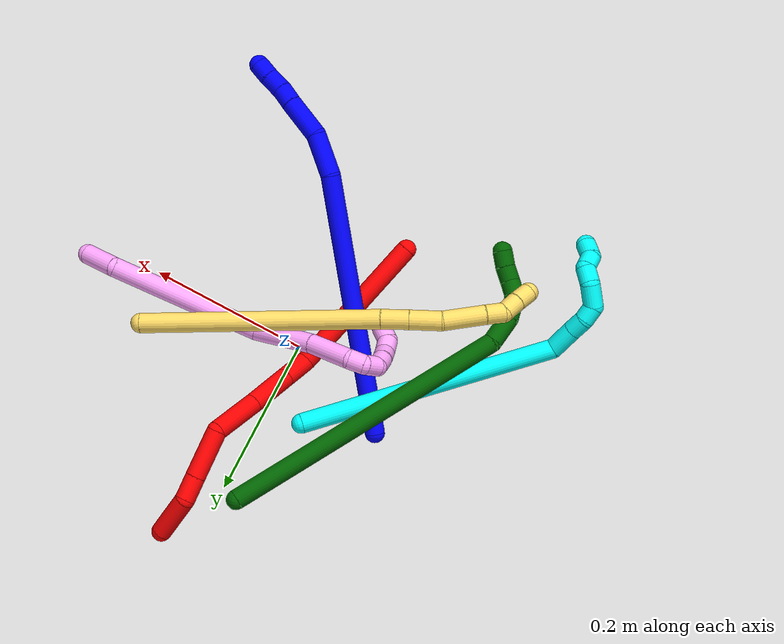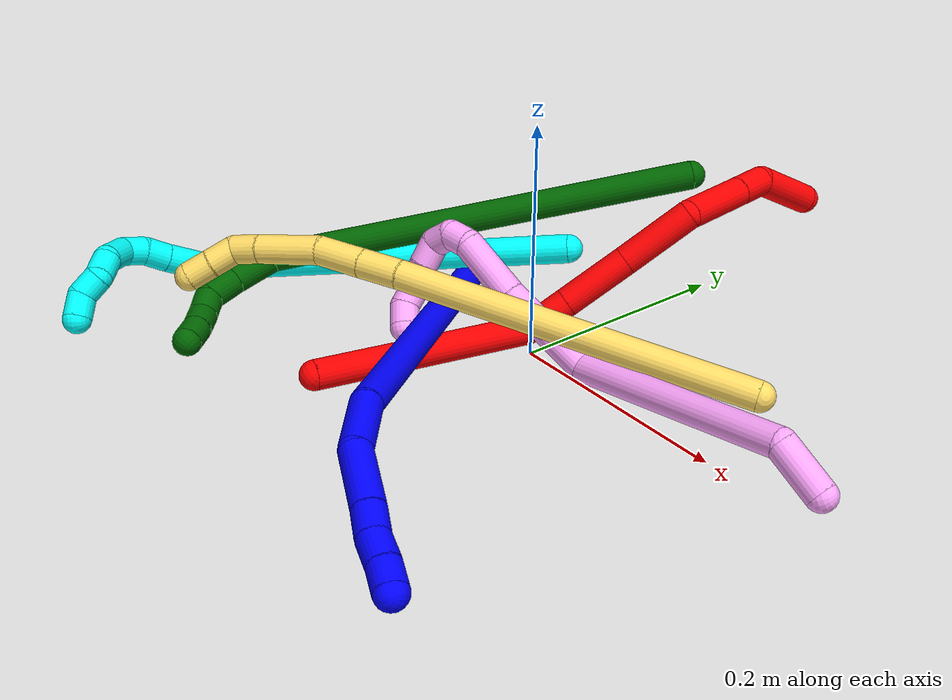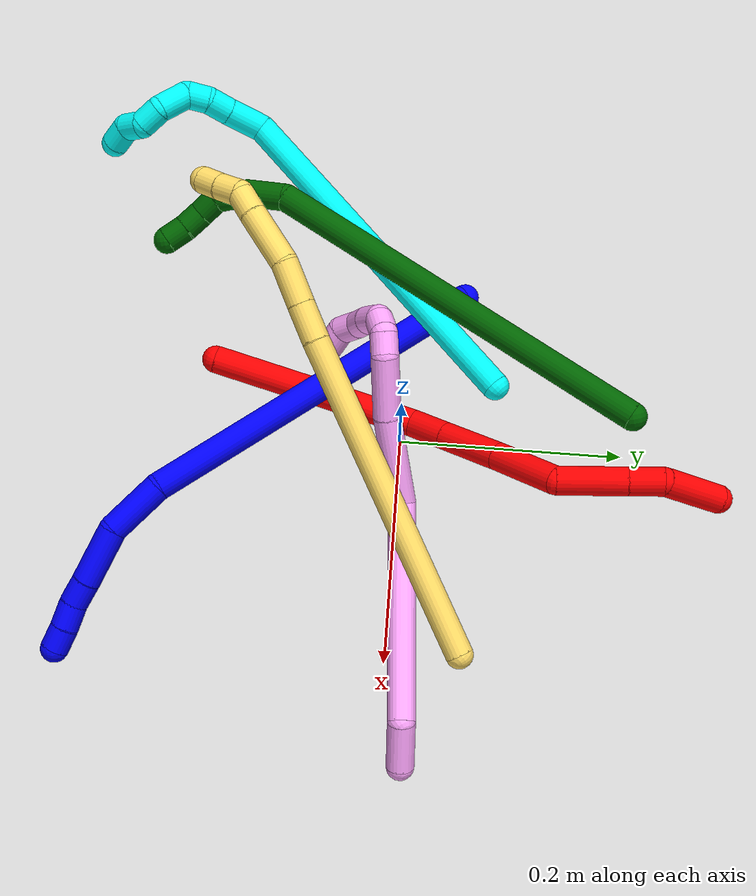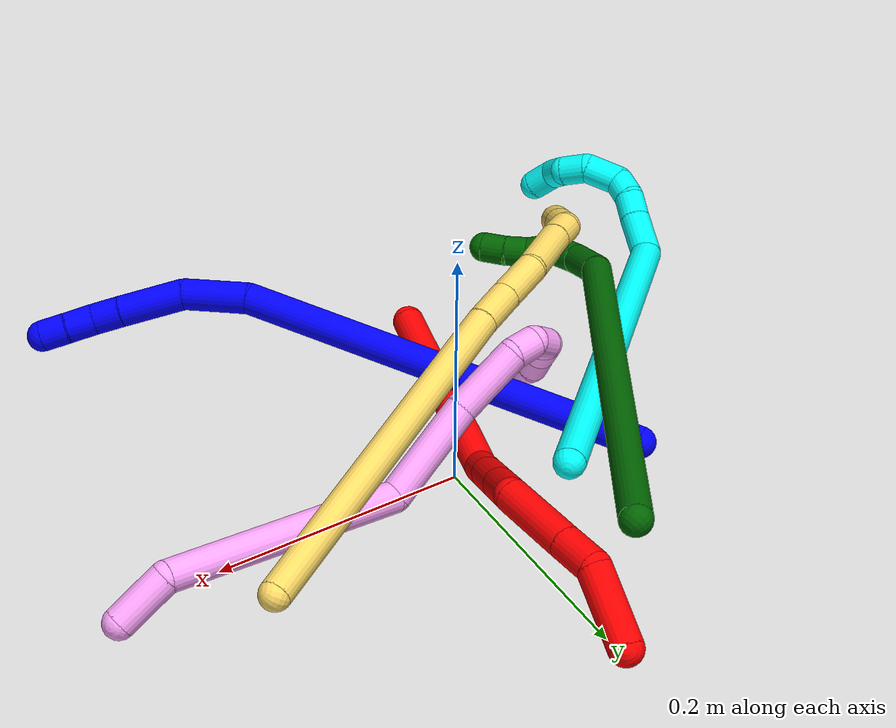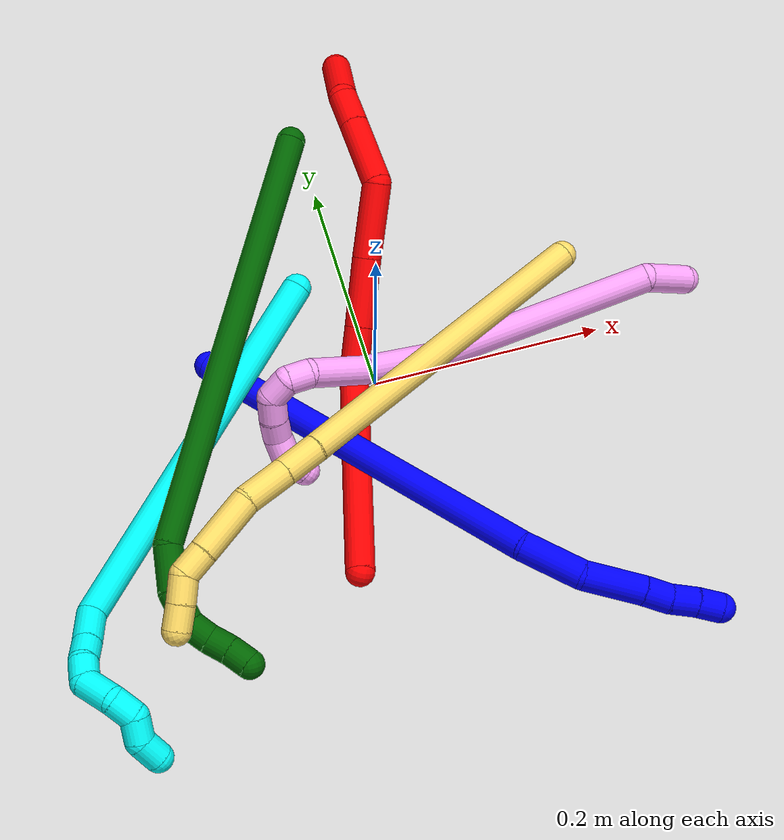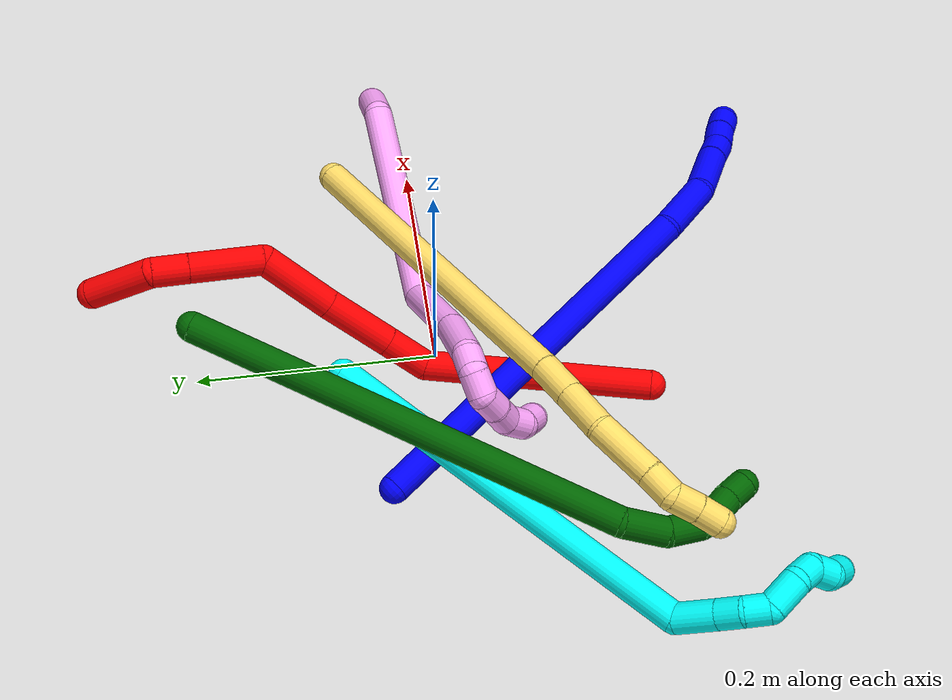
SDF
<sdf version="1.7">
 <world name="default">
  <plugin name="TubeGeneratorPlugin" filename="libtube_generator_plugin.so"/>
  <model name="photoneo_s_sensor">
   <static>1</static>
   <pose>0 0 2 1.57079 1.57079 3.14159</pose>
   <link name="link">
    <inertial><mass>0.1</mass></inertial>
    <sensor name="sensor" type="depth">
     <update_rate>30</update_rate>
     <camera>
      <horizontal_fov>1.22</horizontal_fov>
      <image><width>1920</width><height>1200</height><format>B8G8R8</format></image>
      <clip><near>0.1</near><far>4</far></clip>
      <depth_camera><output>points</output></depth_camera>
     </camera>
     <plugin name="camera_plugin" filename="libgazebo_ros_depth_camera.so">
      <baseline>0.2</baseline>
      <alwaysOn>1</alwaysOn>
      <updateRate>0.0</updateRate>
      <cameraName>camera_ir</cameraName>
      <imageTopicName>/camera/color/image_raw</imageTopicName>
      <cameraInfoTopicName>/camera/color/camera_info</cameraInfoTopicName>
      <depthImageTopicName>/camera/depth/image_raw</depthImageTopicName>
      <depthImageCameraInfoTopicName>/camera/depth/camera_info</depthImageCameraInfoTopicName>
      <pointCloudTopicName>/camera/depth/points</pointCloudTopicName>
      <frameName>fr_optical</frameName>
      <pointCloudCutoff>0.1</pointCloudCutoff>
      <pointCloudCutoffMax>2.0</pointCloudCutoffMax>
      <distortionK1>0</distortionK1>
      <distortionK2>0</distortionK2>
      <distortionK3>0</distortionK3>
      <distortionT1>0</distortionT1>
      <distortionT2>0</distortionT2>
      <CxPrime>0</CxPrime>
      <Cx>0</Cx>
      <Cy>0</Cy>
      <focalLength>0</focalLength>
      <hackBaseline>0</hackBaseline>
     </plugin>
    </sensor>
   </link>
  </model>
  <gravity>0 0 -9.8</gravity>
  <magnetic_field>6e-06 2.3e-05 -4.2e-05</magnetic_field>
  <atmosphere type="adiabatic"/>
  <physics name="default_physics" default="0" type="ode">
   <max_step_size>0.003</max_step_size>
   <real_time_factor>1</real_time_factor>
   <real_time_update_rate>1000</real_time_update_rate>
   <max_contacts>10000</max_contacts>
   <ode>
    <solver>
     <type>quick</type>
     <iters>100</iters>
     <sor>1.3</sor>
     <use_dynamic_moi_rescaling>0</use_dynamic_moi_rescaling>
    </solver>
    <constraints>
     <contact_max_correcting_vel>0</contact_max_correcting_vel>
     <contact_surface_layer>0.001</contact_surface_layer>
     <cfm>0</cfm>
     <erp>0.2</erp>
    </constraints>
   </ode>
  </physics>
  <scene><ambient>0.4 0.4 0.4 1</ambient><background>0.7 0.7 0.7 1</background><shadows>0</shadows></scene>
  <audio><device>default</device></audio>
  <spherical_coordinates>
   <surface_model>EARTH_WGS84</surface_model>
   <latitude_deg>0</latitude_deg>
   <longitude_deg>0</longitude_deg>
   <elevation>0</elevation>
   <heading_deg>0</heading_deg>
  </spherical_coordinates>
  <model name="bin">
   <static>1</static>
   <link name="bottom">
    <collision name="collision-bottom">
     <pose>0 0 -0.01 0 -0 0</pose>
     <geometry><box><size>0.8 0.6 0.02</size></box></geometry>
     <surface>
      <friction><ode><mu>100</mu><mu2>100</mu2></ode></friction>
      <contact><collide_bitmask>65535</collide_bitmask></contact>
     </surface>
    </collision>
   </link>
   <link name="west_wall">
    <collision name="collision-west_wall">
     <pose>-0.41 0 0.1 0 -0 0</pose>
     <geometry><box><size>0.02 0.6 0.2</size></box></geometry>
     <surface>
      <friction><ode><mu>100</mu><mu2>100</mu2></ode></friction>
      <contact><collide_bitmask>65535</collide_bitmask></contact>
     </surface>
    </collision>
   </link>
   <link name="east_wall">
    <collision name="collision-east_wall">
     <pose>0.41 0 0.1 0 -0 0</pose>
     <geometry><box><size>0.02 0.6 0.2</size></box></geometry>
     <surface>
      <friction><ode><mu>100</mu><mu2>100</mu2></ode></friction>
      <contact><collide_bitmask>65535</collide_bitmask></contact>
     </surface>
    </collision>
   </link>
   <link name="south_wall">
    <collision name="collision-south_wall">
     <pose>0 -0.31 0.1 0 -0 0</pose>
     <geometry><box><size>0.8 0.02 0.2</size></box></geometry>
     <surface>
      <friction><ode><mu>100</mu><mu2>100</mu2></ode></friction>
      <contact><collide_bitmask>65535</collide_bitmask></contact>
     </surface>
    </collision>
   </link>
   <link name="north_wall">
    <collision name="collision-north_wall">
     <pose>0 0.31 0.1 0 -0 0</pose>
     <geometry><box><size>0.8 0.02 0.2</size></box></geometry>
     <surface>
      <friction><ode><mu>100</mu><mu2>100</mu2></ode></friction>
      <contact><collide_bitmask>65535</collide_bitmask></contact>
     </surface>
    </collision>
   </link>
  </model>
  <model name="1">
   <static>0</static>
   <link name="1">
    <collision name="collision-cylinder-e_1_1_4">
     <pose>0.047956 -0.038329 0.152147 0.246785 0.296631 0.037057</pose>
     <geometry><cylinder><radius>0.0125</radius><length>0.328131</length></cylinder></geometry>
     <surface>
      <friction><ode><mu>1.16</mu><mu2>1.16</mu2><slip1>0</slip1><slip2>0</slip2></ode></friction>
      <contact><ode><kp>1e+06</kp><kd>1</kd><max_vel>0</max_vel><min_depth>0.001</min_depth></ode></contact>
     </surface>
    </collision>
    <visual name="visual-cylinder-e_1_1_4">
     <pose>0.047956 -0.038329 0.152147 0.246785 0.296631 0.037057</pose>
     <geometry><cylinder><radius>0.0125</radius><length>0.328131</length></cylinder></geometry>
     <material><ambient>0 0 1 1</ambient></material>
    </visual>
    <collision name="collision-cylinder-e_2_4_5">
     <pose>0.109444 -0.085693 0.325374 0.404904 0.533 0.111954</pose>
     <geometry><cylinder><radius>0.0125</radius><length>0.053259</length></cylinder></geometry>
     <surface>
      <friction><ode><mu>1.16</mu><mu2>1.16</mu2><slip1>0</slip1><slip2>0</slip2></ode></friction>
      <contact><ode><kp>1e+06</kp><kd>1</kd><max_vel>0</max_vel><min_depth>0.001</min_depth></ode></contact>
     </surface>
    </collision>
    <visual name="visual-cylinder-e_2_4_5">
     <pose>0.109444 -0.085693 0.325374 0.404904 0.533 0.111954</pose>
     <geometry><cylinder><radius>0.0125</radius><length>0.053259</length></cylinder></geometry>
     <material><ambient>0 0 1 1</ambient></material>
    </visual>
    <collision name="collision-cylinder-e_3_5_6">
     <pose>0.142946 -0.103121 0.360806 0.529217 0.876585 0.252646</pose>
     <geometry><cylinder><radius>0.0125</radius><length>0.051971</length></cylinder></geometry>
     <surface>
      <friction><ode><mu>1.16</mu><mu2>1.16</mu2><slip1>0</slip1><slip2>0</slip2></ode></friction>
      <contact><ode><kp>1e+06</kp><kd>1</kd><max_vel>0</max_vel><min_depth>0.001</min_depth></ode></contact>
     </surface>
    </collision>
    <visual name="visual-cylinder-e_3_5_6">
     <pose>0.142946 -0.103121 0.360806 0.529217 0.876585 0.252646</pose>
     <geometry><cylinder><radius>0.0125</radius><length>0.051971</length></cylinder></geometry>
     <material><ambient>0 0 1 1</ambient></material>
    </visual>
    <collision name="collision-cylinder-e_4_6_7">
     <pose>0.17138 -0.115883 0.381367 0.613027 0.83948 0.280616</pose>
     <geometry><cylinder><radius>0.0125</radius><length>0.022739</length></cylinder></geometry>
     <surface>
      <friction><ode><mu>1.16</mu><mu2>1.16</mu2><slip1>0</slip1><slip2>0</slip2></ode></friction>
      <contact><ode><kp>1e+06</kp><kd>1</kd><max_vel>0</max_vel><min_depth>0.001</min_depth></ode></contact>
     </surface>
    </collision>
    <visual name="visual-cylinder-e_4_6_7">
     <pose>0.17138 -0.115883 0.381367 0.613027 0.83948 0.280616</pose>
     <geometry><cylinder><radius>0.0125</radius><length>0.022739</length></cylinder></geometry>
     <material><ambient>0 0 1 1</ambient></material>
    </visual>
    <collision name="collision-cylinder-e_5_7_8">
     <pose>0.189362 -0.122951 0.39329 0.441394 0.984857 0.239582</pose>
     <geometry><cylinder><radius>0.0125</radius><length>0.02285</length></cylinder></geometry>
     <surface>
      <friction><ode><mu>1.16</mu><mu2>1.16</mu2><slip1>0</slip1><slip2>0</slip2></ode></friction>
      <contact><ode><kp>1e+06</kp><kd>1</kd><max_vel>0</max_vel><min_depth>0.001</min_depth></ode></contact>
     </surface>
    </collision>
    <visual name="visual-cylinder-e_5_7_8">
     <pose>0.189362 -0.122951 0.39329 0.441394 0.984857 0.239582</pose>
     <geometry><cylinder><radius>0.0125</radius><length>0.02285</length></cylinder></geometry>
     <material><ambient>0 0 1 1</ambient></material>
    </visual>
    <collision name="collision-cylinder-e_6_8_2">
     <pose>0.207225 -0.129045 0.404445 0.557817 0.915363 0.280265</pose>
     <geometry><cylinder><radius>0.0125</radius><length>0.021049</length></cylinder></geometry>
     <surface>
      <friction><ode><mu>1.16</mu><mu2>1.16</mu2><slip1>0</slip1><slip2>0</slip2></ode></friction>
      <contact><ode><kp>1e+06</kp><kd>1</kd><max_vel>0</max_vel><min_depth>0.001</min_depth></ode></contact>
     </surface>
    </collision>
    <visual name="visual-cylinder-e_6_8_2">
     <pose>0.207225 -0.129045 0.404445 0.557817 0.915363 0.280265</pose>
     <geometry><cylinder><radius>0.0125</radius><length>0.021049</length></cylinder></geometry>
     <material><ambient>0 0 1 1</ambient></material>
    </visual>
    <collision name="collision-sphere-2">
     <pose>0.215569 -0.132441 0.409887 0 -0 0</pose>
     <geometry><sphere><radius>0.0125</radius></sphere></geometry>
     <surface>
      <friction><ode><mu>1.16</mu><mu2>1.16</mu2><slip1>0</slip1><slip2>0</slip2></ode></friction>
      <contact><ode><kp>1e+06</kp><kd>1</kd><max_vel>0</max_vel><min_depth>0.001</min_depth></ode></contact>
     </surface>
    </collision>
    <visual name="visual-sphere-2">
     <pose>0.215569 -0.132441 0.409887 0 -0 0</pose>
     <geometry><sphere><radius>0.0125</radius></sphere></geometry>
     <material><ambient>0 0 1 1</ambient></material>
    </visual>
    <collision name="collision-sphere-4">
     <pose>0.095913 -0.076658 0.304293 0 -0 0</pose>
     <geometry><sphere><radius>0.0125</radius></sphere></geometry>
     <surface>
      <friction><ode><mu>1.16</mu><mu2>1.16</mu2><slip1>0</slip1><slip2>0</slip2></ode></friction>
      <contact><ode><kp>1e+06</kp><kd>1</kd><max_vel>0</max_vel><min_depth>0.001</min_depth></ode></contact>
     </surface>
    </collision>
    <visual name="visual-sphere-4">
     <pose>0.095913 -0.076658 0.304293 0 -0 0</pose>
     <geometry><sphere><radius>0.0125</radius></sphere></geometry>
     <material><ambient>0 0 1 1</ambient></material>
    </visual>
    <collision name="collision-sphere-1">
     <geometry><sphere><radius>0.0125</radius></sphere></geometry>
     <surface>
      <friction><ode><mu>1.16</mu><mu2>1.16</mu2><slip1>0</slip1><slip2>0</slip2></ode></friction>
      <contact><ode><kp>1e+06</kp><kd>1</kd><max_vel>0</max_vel><min_depth>0.001</min_depth></ode></contact>
     </surface>
    </collision>
    <visual name="visual-sphere-1">
     <geometry><sphere><radius>0.0125</radius></sphere></geometry>
     <material><ambient>0 0 1 1</ambient></material>
    </visual>
    <collision name="collision-sphere-8">
     <pose>0.198881 -0.12565 0.399003 0 -0 0</pose>
     <geometry><sphere><radius>0.0125</radius></sphere></geometry>
     <surface>
      <friction><ode><mu>1.16</mu><mu2>1.16</mu2><slip1>0</slip1><slip2>0</slip2></ode></friction>
      <contact><ode><kp>1e+06</kp><kd>1</kd><max_vel>0</max_vel><min_depth>0.001</min_depth></ode></contact>
     </surface>
    </collision>
    <visual name="visual-sphere-8">
     <pose>0.198881 -0.12565 0.399003 0 -0 0</pose>
     <geometry><sphere><radius>0.0125</radius></sphere></geometry>
     <material><ambient>0 0 1 1</ambient></material>
    </visual>
    <collision name="collision-sphere-5">
     <pose>0.122975 -0.094728 0.346455 0 -0 0</pose>
     <geometry><sphere><radius>0.0125</radius></sphere></geometry>
     <surface>
      <friction><ode><mu>1.16</mu><mu2>1.16</mu2><slip1>0</slip1><slip2>0</slip2></ode></friction>
      <contact><ode><kp>1e+06</kp><kd>1</kd><max_vel>0</max_vel><min_depth>0.001</min_depth></ode></contact>
     </surface>
    </collision>
    <visual name="visual-sphere-5">
     <pose>0.122975 -0.094728 0.346455 0 -0 0</pose>
     <geometry><sphere><radius>0.0125</radius></sphere></geometry>
     <material><ambient>0 0 1 1</ambient></material>
    </visual>
    <collision name="collision-sphere-6">
     <pose>0.162918 -0.111514 0.375157 0 -0 0</pose>
     <geometry><sphere><radius>0.0125</radius></sphere></geometry>
     <surface>
      <friction><ode><mu>1.16</mu><mu2>1.16</mu2><slip1>0</slip1><slip2>0</slip2></ode></friction>
      <contact><ode><kp>1e+06</kp><kd>1</kd><max_vel>0</max_vel><min_depth>0.001</min_depth></ode></contact>
     </surface>
    </collision>
    <visual name="visual-sphere-6">
     <pose>0.162918 -0.111514 0.375157 0 -0 0</pose>
     <geometry><sphere><radius>0.0125</radius></sphere></geometry>
     <material><ambient>0 0 1 1</ambient></material>
    </visual>
    <collision name="collision-sphere-7">
     <pose>0.179842 -0.120252 0.387578 0 -0 0</pose>
     <geometry><sphere><radius>0.0125</radius></sphere></geometry>
     <surface>
      <friction><ode><mu>1.16</mu><mu2>1.16</mu2><slip1>0</slip1><slip2>0</slip2></ode></friction>
      <contact><ode><kp>1e+06</kp><kd>1</kd><max_vel>0</max_vel><min_depth>0.001</min_depth></ode></contact>
     </surface>
    </collision>
    <visual name="visual-sphere-7">
     <pose>0.179842 -0.120252 0.387578 0 -0 0</pose>
     <geometry><sphere><radius>0.0125</radius></sphere></geometry>
     <material><ambient>0 0 1 1</ambient></material>
    </visual>
    <inertial>
     <pose>0.08316 -0.061322 0.224353 0 -0 0</pose>
     <mass>0.5</mass>
     <inertia>
      <ixx>0.002976</ixx>
      <ixy>0</ixy>
      <ixz>0</ixz>
      <iyy>0.003004</iyy>
      <iyz>0</iyz>
      <izz>-0.000153</izz>
     </inertia>
    </inertial>
   </link>
   <pose>-0.134696 0.0501 0.011632 1.05407 0.316688 0.290437</pose>
  </model>
  <model name="2">
   <static>0</static>
   <link name="2">
    <collision name="collision-cylinder-e_1_1_4">
     <pose>0.028302 0.067066 0.059339 -0.846456 0.306113 -0.138752</pose>
     <geometry><cylinder><radius>0.0125</radius><length>0.187829</length></cylinder></geometry>
     <surface>
      <friction><ode><mu>1.16</mu><mu2>1.16</mu2><slip1>0</slip1><slip2>0</slip2></ode></friction>
      <contact><ode><kp>1e+06</kp><kd>1</kd><max_vel>0</max_vel><min_depth>0.001</min_depth></ode></contact>
     </surface>
    </collision>
    <visual name="visual-cylinder-e_1_1_4">
     <pose>0.028302 0.067066 0.059339 -0.846456 0.306113 -0.138752</pose>
     <geometry><cylinder><radius>0.0125</radius><length>0.187829</length></cylinder></geometry>
     <material><ambient>1 0 0 1</ambient></material>
    </visual>
    <collision name="collision-cylinder-e_2_4_5">
     <pose>0.057374 0.139723 0.137336 -0.291091 0.039547 -0.005798</pose>
     <geometry><cylinder><radius>0.0125</radius><length>0.038988</length></cylinder></geometry>
     <surface>
      <friction><ode><mu>1.16</mu><mu2>1.16</mu2><slip1>0</slip1><slip2>0</slip2></ode></friction>
      <contact><ode><kp>1e+06</kp><kd>1</kd><max_vel>0</max_vel><min_depth>0.001</min_depth></ode></contact>
     </surface>
    </collision>
    <visual name="visual-cylinder-e_2_4_5">
     <pose>0.057374 0.139723 0.137336 -0.291091 0.039547 -0.005798</pose>
     <geometry><cylinder><radius>0.0125</radius><length>0.038988</length></cylinder></geometry>
     <material><ambient>1 0 0 1</ambient></material>
    </visual>
    <collision name="collision-cylinder-e_3_5_6">
     <pose>0.059287 0.153972 0.184291 -0.296955 0.038604 -0.005775</pose>
     <geometry><cylinder><radius>0.0125</radius><length>0.059225</length></cylinder></geometry>
     <surface>
      <friction><ode><mu>1.16</mu><mu2>1.16</mu2><slip1>0</slip1><slip2>0</slip2></ode></friction>
      <contact><ode><kp>1e+06</kp><kd>1</kd><max_vel>0</max_vel><min_depth>0.001</min_depth></ode></contact>
     </surface>
    </collision>
    <visual name="visual-cylinder-e_3_5_6">
     <pose>0.059287 0.153972 0.184291 -0.296955 0.038604 -0.005775</pose>
     <geometry><cylinder><radius>0.0125</radius><length>0.059225</length></cylinder></geometry>
     <material><ambient>1 0 0 1</ambient></material>
    </visual>
    <collision name="collision-cylinder-e_4_6_7">
     <pose>0.061615 0.170822 0.243768 -0.256916 0.036744 -0.004747</pose>
     <geometry><cylinder><radius>0.0125</radius><length>0.064522</length></cylinder></geometry>
     <surface>
      <friction><ode><mu>1.16</mu><mu2>1.16</mu2><slip1>0</slip1><slip2>0</slip2></ode></friction>
      <contact><ode><kp>1e+06</kp><kd>1</kd><max_vel>0</max_vel><min_depth>0.001</min_depth></ode></contact>
     </surface>
    </collision>
    <visual name="visual-cylinder-e_4_6_7">
     <pose>0.061615 0.170822 0.243768 -0.256916 0.036744 -0.004747</pose>
     <geometry><cylinder><radius>0.0125</radius><length>0.064522</length></cylinder></geometry>
     <material><ambient>1 0 0 1</ambient></material>
    </visual>
    <collision name="collision-cylinder-e_5_7_8">
     <pose>0.063912 0.204357 0.291869 -0.982113 0.036454 -0.019495</pose>
     <geometry><cylinder><radius>0.0125</radius><length>0.060985</length></cylinder></geometry>
     <surface>
      <friction><ode><mu>1.16</mu><mu2>1.16</mu2><slip1>0</slip1><slip2>0</slip2></ode></friction>
      <contact><ode><kp>1e+06</kp><kd>1</kd><max_vel>0</max_vel><min_depth>0.001</min_depth></ode></contact>
     </surface>
    </collision>
    <visual name="visual-cylinder-e_5_7_8">
     <pose>0.063912 0.204357 0.291869 -0.982113 0.036454 -0.019495</pose>
     <geometry><cylinder><radius>0.0125</radius><length>0.060985</length></cylinder></geometry>
     <material><ambient>1 0 0 1</ambient></material>
    </visual>
    <collision name="collision-cylinder-e_6_8_9">
     <pose>0.065418 0.242353 0.317221 -0.982987 0.02594 -0.013887</pose>
     <geometry><cylinder><radius>0.0125</radius><length>0.030422</length></cylinder></geometry>
     <surface>
      <friction><ode><mu>1.16</mu><mu2>1.16</mu2><slip1>0</slip1><slip2>0</slip2></ode></friction>
      <contact><ode><kp>1e+06</kp><kd>1</kd><max_vel>0</max_vel><min_depth>0.001</min_depth></ode></contact>
     </surface>
    </collision>
    <visual name="visual-cylinder-e_6_8_9">
     <pose>0.065418 0.242353 0.317221 -0.982987 0.02594 -0.013887</pose>
     <geometry><cylinder><radius>0.0125</radius><length>0.030422</length></cylinder></geometry>
     <material><ambient>1 0 0 1</ambient></material>
    </visual>
    <collision name="collision-cylinder-e_7_9_2">
     <pose>0.079509 0.280026 0.330973 -1.3613 0.491622 -0.400845</pose>
     <geometry><cylinder><radius>0.0125</radius><length>0.05803</length></cylinder></geometry>
     <surface>
      <friction><ode><mu>1.16</mu><mu2>1.16</mu2><slip1>0</slip1><slip2>0</slip2></ode></friction>
      <contact><ode><kp>1e+06</kp><kd>1</kd><max_vel>0</max_vel><min_depth>0.001</min_depth></ode></contact>
     </surface>
    </collision>
    <visual name="visual-cylinder-e_7_9_2">
     <pose>0.079509 0.280026 0.330973 -1.3613 0.491622 -0.400845</pose>
     <geometry><cylinder><radius>0.0125</radius><length>0.05803</length></cylinder></geometry>
     <material><ambient>1 0 0 1</ambient></material>
    </visual>
    <collision name="collision-sphere-2">
     <pose>0.093206 0.305045 0.336292 0 -0 0</pose>
     <geometry><sphere><radius>0.0125</radius></sphere></geometry>
     <surface>
      <friction><ode><mu>1.16</mu><mu2>1.16</mu2><slip1>0</slip1><slip2>0</slip2></ode></friction>
      <contact><ode><kp>1e+06</kp><kd>1</kd><max_vel>0</max_vel><min_depth>0.001</min_depth></ode></contact>
     </surface>
    </collision>
    <visual name="visual-sphere-2">
     <pose>0.093206 0.305045 0.336292 0 -0 0</pose>
     <geometry><sphere><radius>0.0125</radius></sphere></geometry>
     <material><ambient>1 0 0 1</ambient></material>
    </visual>
    <collision name="collision-sphere-9">
     <pose>0.065812 0.255006 0.325653 0 -0 0</pose>
     <geometry><sphere><radius>0.0125</radius></sphere></geometry>
     <surface>
      <friction><ode><mu>1.16</mu><mu2>1.16</mu2><slip1>0</slip1><slip2>0</slip2></ode></friction>
      <contact><ode><kp>1e+06</kp><kd>1</kd><max_vel>0</max_vel><min_depth>0.001</min_depth></ode></contact>
     </surface>
    </collision>
    <visual name="visual-sphere-9">
     <pose>0.065812 0.255006 0.325653 0 -0 0</pose>
     <geometry><sphere><radius>0.0125</radius></sphere></geometry>
     <material><ambient>1 0 0 1</ambient></material>
    </visual>
    <collision name="collision-sphere-4">
     <pose>0.056603 0.134132 0.118677 0 -0 0</pose>
     <geometry><sphere><radius>0.0125</radius></sphere></geometry>
     <surface>
      <friction><ode><mu>1.16</mu><mu2>1.16</mu2><slip1>0</slip1><slip2>0</slip2></ode></friction>
      <contact><ode><kp>1e+06</kp><kd>1</kd><max_vel>0</max_vel><min_depth>0.001</min_depth></ode></contact>
     </surface>
    </collision>
    <visual name="visual-sphere-4">
     <pose>0.056603 0.134132 0.118677 0 -0 0</pose>
     <geometry><sphere><radius>0.0125</radius></sphere></geometry>
     <material><ambient>1 0 0 1</ambient></material>
    </visual>
    <collision name="collision-sphere-1">
     <geometry><sphere><radius>0.0125</radius></sphere></geometry>
     <surface>
      <friction><ode><mu>1.16</mu><mu2>1.16</mu2><slip1>0</slip1><slip2>0</slip2></ode></friction>
      <contact><ode><kp>1e+06</kp><kd>1</kd><max_vel>0</max_vel><min_depth>0.001</min_depth></ode></contact>
     </surface>
    </collision>
    <visual name="visual-sphere-1">
     <geometry><sphere><radius>0.0125</radius></sphere></geometry>
     <material><ambient>1 0 0 1</ambient></material>
    </visual>
    <collision name="collision-sphere-8">
     <pose>0.065023 0.229699 0.308789 0 -0 0</pose>
     <geometry><sphere><radius>0.0125</radius></sphere></geometry>
     <surface>
      <friction><ode><mu>1.16</mu><mu2>1.16</mu2><slip1>0</slip1><slip2>0</slip2></ode></friction>
      <contact><ode><kp>1e+06</kp><kd>1</kd><max_vel>0</max_vel><min_depth>0.001</min_depth></ode></contact>
     </surface>
    </collision>
    <visual name="visual-sphere-8">
     <pose>0.065023 0.229699 0.308789 0 -0 0</pose>
     <geometry><sphere><radius>0.0125</radius></sphere></geometry>
     <material><ambient>1 0 0 1</ambient></material>
    </visual>
    <collision name="collision-sphere-5">
     <pose>0.058145 0.145313 0.155996 0 -0 0</pose>
     <geometry><sphere><radius>0.0125</radius></sphere></geometry>
     <surface>
      <friction><ode><mu>1.16</mu><mu2>1.16</mu2><slip1>0</slip1><slip2>0</slip2></ode></friction>
      <contact><ode><kp>1e+06</kp><kd>1</kd><max_vel>0</max_vel><min_depth>0.001</min_depth></ode></contact>
     </surface>
    </collision>
    <visual name="visual-sphere-5">
     <pose>0.058145 0.145313 0.155996 0 -0 0</pose>
     <geometry><sphere><radius>0.0125</radius></sphere></geometry>
     <material><ambient>1 0 0 1</ambient></material>
    </visual>
    <collision name="collision-sphere-6">
     <pose>0.06043 0.16263 0.212587 0 -0 0</pose>
     <geometry><sphere><radius>0.0125</radius></sphere></geometry>
     <surface>
      <friction><ode><mu>1.16</mu><mu2>1.16</mu2><slip1>0</slip1><slip2>0</slip2></ode></friction>
      <contact><ode><kp>1e+06</kp><kd>1</kd><max_vel>0</max_vel><min_depth>0.001</min_depth></ode></contact>
     </surface>
    </collision>
    <visual name="visual-sphere-6">
     <pose>0.06043 0.16263 0.212587 0 -0 0</pose>
     <geometry><sphere><radius>0.0125</radius></sphere></geometry>
     <material><ambient>1 0 0 1</ambient></material>
    </visual>
    <collision name="collision-sphere-7">
     <pose>0.062801 0.179014 0.274949 0 -0 0</pose>
     <geometry><sphere><radius>0.0125</radius></sphere></geometry>
     <surface>
      <friction><ode><mu>1.16</mu><mu2>1.16</mu2><slip1>0</slip1><slip2>0</slip2></ode></friction>
      <contact><ode><kp>1e+06</kp><kd>1</kd><max_vel>0</max_vel><min_depth>0.001</min_depth></ode></contact>
     </surface>
    </collision>
    <visual name="visual-sphere-7">
     <pose>0.062801 0.179014 0.274949 0 -0 0</pose>
     <geometry><sphere><radius>0.0125</radius></sphere></geometry>
     <material><ambient>1 0 0 1</ambient></material>
    </visual>
    <inertial>
     <pose>0.051082 0.148541 0.179598 0 -0 0</pose>
     <mass>0.5</mass>
     <inertia>
      <ixx>0.000546</ixx>
      <ixy>0</ixy>
      <ixz>0</ixz>
      <iyy>0.000397</iyy>
      <iyz>0</iyz>
      <izz>-0.000604</izz>
     </inertia>
    </inertial>
   </link>
   <pose>-0.061381 -0.171384 0.011498 -0.504599 0.603842 0.130147</pose>
  </model>
  <model name="3">
   <static>0</static>
   <link name="3">
    <collision name="collision-cylinder-e_1_1_4">
     <pose>-0.004537 -0.011425 0.164679 0.069264 -0.027478 -0.000952</pose>
     <geometry><cylinder><radius>0.0125</radius><length>0.330275</length></cylinder></geometry>
     <surface>
      <friction><ode><mu>1.16</mu><mu2>1.16</mu2><slip1>0</slip1><slip2>0</slip2></ode></friction>
      <contact><ode><kp>1e+06</kp><kd>1</kd><max_vel>0</max_vel><min_depth>0.001</min_depth></ode></contact>
     </surface>
    </collision>
    <visual name="visual-cylinder-e_1_1_4">
     <pose>-0.004537 -0.011425 0.164679 0.069264 -0.027478 -0.000952</pose>
     <geometry><cylinder><radius>0.0125</radius><length>0.330275</length></cylinder></geometry>
     <material><ambient>0.003922 1 0.996078 1</ambient></material>
    </visual>
    <collision name="collision-cylinder-e_2_4_5">
     <pose>-0.001831 -0.014619 0.34321 -0.536089 0.422467 -0.117653</pose>
     <geometry><cylinder><radius>0.0125</radius><length>0.03533</length></cylinder></geometry>
     <surface>
      <friction><ode><mu>1.16</mu><mu2>1.16</mu2><slip1>0</slip1><slip2>0</slip2></ode></friction>
      <contact><ode><kp>1e+06</kp><kd>1</kd><max_vel>0</max_vel><min_depth>0.001</min_depth></ode></contact>
     </surface>
    </collision>
    <visual name="visual-cylinder-e_2_4_5">
     <pose>-0.001831 -0.014619 0.34321 -0.536089 0.422467 -0.117653</pose>
     <geometry><cylinder><radius>0.0125</radius><length>0.03533</length></cylinder></geometry>
     <material><ambient>0.003922 1 0.996078 1</ambient></material>
    </visual>
    <collision name="collision-cylinder-e_3_5_6">
     <pose>0.009366 -0.000868 0.365161 -0.598392 0.383398 -0.119589</pose>
     <geometry><cylinder><radius>0.0125</radius><length>0.021141</length></cylinder></geometry>
     <surface>
      <friction><ode><mu>1.16</mu><mu2>1.16</mu2><slip1>0</slip1><slip2>0</slip2></ode></friction>
      <contact><ode><kp>1e+06</kp><kd>1</kd><max_vel>0</max_vel><min_depth>0.001</min_depth></ode></contact>
     </surface>
    </collision>
    <visual name="visual-cylinder-e_3_5_6">
     <pose>0.009366 -0.000868 0.365161 -0.598392 0.383398 -0.119589</pose>
     <geometry><cylinder><radius>0.0125</radius><length>0.021141</length></cylinder></geometry>
     <material><ambient>0.003922 1 0.996078 1</ambient></material>
    </visual>
    <collision name="collision-cylinder-e_4_6_7">
     <pose>0.01917 0.007432 0.380981 -0.345345 0.619381 -0.111502</pose>
     <geometry><cylinder><radius>0.0125</radius><length>0.020153</length></cylinder></geometry>
     <surface>
      <friction><ode><mu>1.16</mu><mu2>1.16</mu2><slip1>0</slip1><slip2>0</slip2></ode></friction>
      <contact><ode><kp>1e+06</kp><kd>1</kd><max_vel>0</max_vel><min_depth>0.001</min_depth></ode></contact>
     </surface>
    </collision>
    <visual name="visual-cylinder-e_4_6_7">
     <pose>0.01917 0.007432 0.380981 -0.345345 0.619381 -0.111502</pose>
     <geometry><cylinder><radius>0.0125</radius><length>0.020153</length></cylinder></geometry>
     <material><ambient>0.003922 1 0.996078 1</ambient></material>
    </visual>
    <collision name="collision-cylinder-e_5_7_8">
     <pose>0.039156 0.013829 0.390536 -1.10181 1.29128 -0.86693</pose>
     <geometry><cylinder><radius>0.0125</radius><length>0.029414</length></cylinder></geometry>
     <surface>
      <friction><ode><mu>1.16</mu><mu2>1.16</mu2><slip1>0</slip1><slip2>0</slip2></ode></friction>
      <contact><ode><kp>1e+06</kp><kd>1</kd><max_vel>0</max_vel><min_depth>0.001</min_depth></ode></contact>
     </surface>
    </collision>
    <visual name="visual-cylinder-e_5_7_8">
     <pose>0.039156 0.013829 0.390536 -1.10181 1.29128 -0.86693</pose>
     <geometry><cylinder><radius>0.0125</radius><length>0.029414</length></cylinder></geometry>
     <material><ambient>0.003922 1 0.996078 1</ambient></material>
    </visual>
    <collision name="collision-cylinder-e_6_8_9">
     <pose>0.063553 0.014247 0.39337 1.2679 1.25487 0.979625</pose>
     <geometry><cylinder><radius>0.0125</radius><length>0.021591</length></cylinder></geometry>
     <surface>
      <friction><ode><mu>1.16</mu><mu2>1.16</mu2><slip1>0</slip1><slip2>0</slip2></ode></friction>
      <contact><ode><kp>1e+06</kp><kd>1</kd><max_vel>0</max_vel><min_depth>0.001</min_depth></ode></contact>
     </surface>
    </collision>
    <visual name="visual-cylinder-e_6_8_9">
     <pose>0.063553 0.014247 0.39337 1.2679 1.25487 0.979625</pose>
     <geometry><cylinder><radius>0.0125</radius><length>0.021591</length></cylinder></geometry>
     <material><ambient>0.003922 1 0.996078 1</ambient></material>
    </visual>
    <collision name="collision-cylinder-e_7_9_10">
     <pose>0.079453 0.005327 0.40076 0.730019 0.581707 0.227787</pose>
     <geometry><cylinder><radius>0.0125</radius><length>0.020525</length></cylinder></geometry>
     <surface>
      <friction><ode><mu>1.16</mu><mu2>1.16</mu2><slip1>0</slip1><slip2>0</slip2></ode></friction>
      <contact><ode><kp>1e+06</kp><kd>1</kd><max_vel>0</max_vel><min_depth>0.001</min_depth></ode></contact>
     </surface>
    </collision>
    <visual name="visual-cylinder-e_7_9_10">
     <pose>0.079453 0.005327 0.40076 0.730019 0.581707 0.227787</pose>
     <geometry><cylinder><radius>0.0125</radius><length>0.020525</length></cylinder></geometry>
     <material><ambient>0.003922 1 0.996078 1</ambient></material>
    </visual>
    <collision name="collision-cylinder-e_8_10_2">
     <pose>0.093371 -0.007269 0.407845 1.47003 0.87507 0.800114</pose>
     <geometry><cylinder><radius>0.0125</radius><length>0.021571</length></cylinder></geometry>
     <surface>
      <friction><ode><mu>1.16</mu><mu2>1.16</mu2><slip1>0</slip1><slip2>0</slip2></ode></friction>
      <contact><ode><kp>1e+06</kp><kd>1</kd><max_vel>0</max_vel><min_depth>0.001</min_depth></ode></contact>
     </surface>
    </collision>
    <visual name="visual-cylinder-e_8_10_2">
     <pose>0.093371 -0.007269 0.407845 1.47003 0.87507 0.800114</pose>
     <geometry><cylinder><radius>0.0125</radius><length>0.021571</length></cylinder></geometry>
     <material><ambient>0.003922 1 0.996078 1</ambient></material>
    </visual>
    <collision name="collision-sphere-2">
     <pose>0.101649 -0.014147 0.40854 0 -0 0</pose>
     <geometry><sphere><radius>0.0125</radius></sphere></geometry>
     <surface>
      <friction><ode><mu>1.16</mu><mu2>1.16</mu2><slip1>0</slip1><slip2>0</slip2></ode></friction>
      <contact><ode><kp>1e+06</kp><kd>1</kd><max_vel>0</max_vel><min_depth>0.001</min_depth></ode></contact>
     </surface>
    </collision>
    <visual name="visual-sphere-2">
     <pose>0.101649 -0.014147 0.40854 0 -0 0</pose>
     <geometry><sphere><radius>0.0125</radius></sphere></geometry>
     <material><ambient>0.003922 1 0.996078 1</ambient></material>
    </visual>
    <collision name="collision-sphere-10">
     <pose>0.085092 -0.000391 0.407149 0 -0 0</pose>
     <geometry><sphere><radius>0.0125</radius></sphere></geometry>
     <surface>
      <friction><ode><mu>1.16</mu><mu2>1.16</mu2><slip1>0</slip1><slip2>0</slip2></ode></friction>
      <contact><ode><kp>1e+06</kp><kd>1</kd><max_vel>0</max_vel><min_depth>0.001</min_depth></ode></contact>
     </surface>
    </collision>
    <visual name="visual-sphere-10">
     <pose>0.085092 -0.000391 0.407149 0 -0 0</pose>
     <geometry><sphere><radius>0.0125</radius></sphere></geometry>
     <material><ambient>0.003922 1 0.996078 1</ambient></material>
    </visual>
    <collision name="collision-sphere-9">
     <pose>0.073814 0.011046 0.394371 0 -0 0</pose>
     <geometry><sphere><radius>0.0125</radius></sphere></geometry>
     <surface>
      <friction><ode><mu>1.16</mu><mu2>1.16</mu2><slip1>0</slip1><slip2>0</slip2></ode></friction>
      <contact><ode><kp>1e+06</kp><kd>1</kd><max_vel>0</max_vel><min_depth>0.001</min_depth></ode></contact>
     </surface>
    </collision>
    <visual name="visual-sphere-9">
     <pose>0.073814 0.011046 0.394371 0 -0 0</pose>
     <geometry><sphere><radius>0.0125</radius></sphere></geometry>
     <material><ambient>0.003922 1 0.996078 1</ambient></material>
    </visual>
    <collision name="collision-sphere-4">
     <pose>-0.009074 -0.022849 0.329358 0 -0 0</pose>
     <geometry><sphere><radius>0.0125</radius></sphere></geometry>
     <surface>
      <friction><ode><mu>1.16</mu><mu2>1.16</mu2><slip1>0</slip1><slip2>0</slip2></ode></friction>
      <contact><ode><kp>1e+06</kp><kd>1</kd><max_vel>0</max_vel><min_depth>0.001</min_depth></ode></contact>
     </surface>
    </collision>
    <visual name="visual-sphere-4">
     <pose>-0.009074 -0.022849 0.329358 0 -0 0</pose>
     <geometry><sphere><radius>0.0125</radius></sphere></geometry>
     <material><ambient>0.003922 1 0.996078 1</ambient></material>
    </visual>
    <collision name="collision-sphere-1">
     <geometry><sphere><radius>0.0125</radius></sphere></geometry>
     <surface>
      <friction><ode><mu>1.16</mu><mu2>1.16</mu2><slip1>0</slip1><slip2>0</slip2></ode></friction>
      <contact><ode><kp>1e+06</kp><kd>1</kd><max_vel>0</max_vel><min_depth>0.001</min_depth></ode></contact>
     </surface>
    </collision>
    <visual name="visual-sphere-1">
     <geometry><sphere><radius>0.0125</radius></sphere></geometry>
     <material><ambient>0.003922 1 0.996078 1</ambient></material>
    </visual>
    <collision name="collision-sphere-8">
     <pose>0.053292 0.017448 0.39237 0 -0 0</pose>
     <geometry><sphere><radius>0.0125</radius></sphere></geometry>
     <surface>
      <friction><ode><mu>1.16</mu><mu2>1.16</mu2><slip1>0</slip1><slip2>0</slip2></ode></friction>
      <contact><ode><kp>1e+06</kp><kd>1</kd><max_vel>0</max_vel><min_depth>0.001</min_depth></ode></contact>
     </surface>
    </collision>
    <visual name="visual-sphere-8">
     <pose>0.053292 0.017448 0.39237 0 -0 0</pose>
     <geometry><sphere><radius>0.0125</radius></sphere></geometry>
     <material><ambient>0.003922 1 0.996078 1</ambient></material>
    </visual>
    <collision name="collision-sphere-5">
     <pose>0.005412 -0.00639 0.357062 0 -0 0</pose>
     <geometry><sphere><radius>0.0125</radius></sphere></geometry>
     <surface>
      <friction><ode><mu>1.16</mu><mu2>1.16</mu2><slip1>0</slip1><slip2>0</slip2></ode></friction>
      <contact><ode><kp>1e+06</kp><kd>1</kd><max_vel>0</max_vel><min_depth>0.001</min_depth></ode></contact>
     </surface>
    </collision>
    <visual name="visual-sphere-5">
     <pose>0.005412 -0.00639 0.357062 0 -0 0</pose>
     <geometry><sphere><radius>0.0125</radius></sphere></geometry>
     <material><ambient>0.003922 1 0.996078 1</ambient></material>
    </visual>
    <collision name="collision-sphere-6">
     <pose>0.01332 0.004655 0.373261 0 -0 0</pose>
     <geometry><sphere><radius>0.0125</radius></sphere></geometry>
     <surface>
      <friction><ode><mu>1.16</mu><mu2>1.16</mu2><slip1>0</slip1><slip2>0</slip2></ode></friction>
      <contact><ode><kp>1e+06</kp><kd>1</kd><max_vel>0</max_vel><min_depth>0.001</min_depth></ode></contact>
     </surface>
    </collision>
    <visual name="visual-sphere-6">
     <pose>0.01332 0.004655 0.373261 0 -0 0</pose>
     <geometry><sphere><radius>0.0125</radius></sphere></geometry>
     <material><ambient>0.003922 1 0.996078 1</ambient></material>
    </visual>
    <collision name="collision-sphere-7">
     <pose>0.025019 0.01021 0.388702 0 -0 0</pose>
     <geometry><sphere><radius>0.0125</radius></sphere></geometry>
     <surface>
      <friction><ode><mu>1.16</mu><mu2>1.16</mu2><slip1>0</slip1><slip2>0</slip2></ode></friction>
      <contact><ode><kp>1e+06</kp><kd>1</kd><max_vel>0</max_vel><min_depth>0.001</min_depth></ode></contact>
     </surface>
    </collision>
    <visual name="visual-sphere-7">
     <pose>0.025019 0.01021 0.388702 0 -0 0</pose>
     <geometry><sphere><radius>0.0125</radius></sphere></geometry>
     <material><ambient>0.003922 1 0.996078 1</ambient></material>
    </visual>
    <inertial>
     <pose>0.01038 -0.006983 0.237833 0 -0 0</pose>
     <mass>0.5</mass>
     <inertia>
      <ixx>0.003029</ixx>
      <ixy>0</ixy>
      <ixz>0</ixz>
      <iyy>0.003018</iyy>
      <iyz>0</iyz>
      <izz>0.000311</izz>
     </inertia>
    </inertial>
   </link>
   <pose>-0.047371 0.080367 0.053488 1.62988 0.027435 -0.767369</pose>
  </model>
  <model name="4">
   <static>0</static>
   <link name="4">
    <collision name="collision-cylinder-e_1_1_4">
     <pose>-0.020271 0.001698 0.009768 -0.172096 -1.1159 0.107566</pose>
     <geometry><cylinder><radius>0.0125</radius><length>0.045132</length></cylinder></geometry>
     <surface>
      <friction><ode><mu>1.16</mu><mu2>1.16</mu2><slip1>0</slip1><slip2>0</slip2></ode></friction>
      <contact><ode><kp>1e+06</kp><kd>1</kd><max_vel>0</max_vel><min_depth>0.001</min_depth></ode></contact>
     </surface>
    </collision>
    <visual name="visual-cylinder-e_1_1_4">
     <pose>-0.020271 0.001698 0.009768 -0.172096 -1.1159 0.107566</pose>
     <geometry><cylinder><radius>0.0125</radius><length>0.045132</length></cylinder></geometry>
     <material><ambient>1 0.65098 0.996078 1</ambient></material>
    </visual>
    <collision name="collision-cylinder-e_2_4_5">
     <pose>-0.088568 -0.020778 0.100567 0.289923 -0.516522 -0.077089</pose>
     <geometry><cylinder><radius>0.0125</radius><length>0.194491</length></cylinder></geometry>
     <surface>
      <friction><ode><mu>1.16</mu><mu2>1.16</mu2><slip1>0</slip1><slip2>0</slip2></ode></friction>
      <contact><ode><kp>1e+06</kp><kd>1</kd><max_vel>0</max_vel><min_depth>0.001</min_depth></ode></contact>
     </surface>
    </collision>
    <visual name="visual-cylinder-e_2_4_5">
     <pose>-0.088568 -0.020778 0.100567 0.289923 -0.516522 -0.077089</pose>
     <geometry><cylinder><radius>0.0125</radius><length>0.194491</length></cylinder></geometry>
     <material><ambient>1 0.65098 0.996078 1</ambient></material>
    </visual>
    <collision name="collision-cylinder-e_3_5_6">
     <pose>-0.170922 -0.03552 0.202901 -0.416768 -0.974528 0.223159</pose>
     <geometry><cylinder><radius>0.0125</radius><length>0.082976</length></cylinder></geometry>
     <surface>
      <friction><ode><mu>1.16</mu><mu2>1.16</mu2><slip1>0</slip1><slip2>0</slip2></ode></friction>
      <contact><ode><kp>1e+06</kp><kd>1</kd><max_vel>0</max_vel><min_depth>0.001</min_depth></ode></contact>
     </surface>
    </collision>
    <visual name="visual-cylinder-e_3_5_6">
     <pose>-0.170922 -0.03552 0.202901 -0.416768 -0.974528 0.223159</pose>
     <geometry><cylinder><radius>0.0125</radius><length>0.082976</length></cylinder></geometry>
     <material><ambient>1 0.65098 0.996078 1</ambient></material>
    </visual>
    <collision name="collision-cylinder-e_4_6_7">
     <pose>-0.230074 -0.022773 0.237577 -0.24307 -1.06409 0.143549</pose>
     <geometry><cylinder><radius>0.0125</radius><length>0.05678</length></cylinder></geometry>
     <surface>
      <friction><ode><mu>1.16</mu><mu2>1.16</mu2><slip1>0</slip1><slip2>0</slip2></ode></friction>
      <contact><ode><kp>1e+06</kp><kd>1</kd><max_vel>0</max_vel><min_depth>0.001</min_depth></ode></contact>
     </surface>
    </collision>
    <visual name="visual-cylinder-e_4_6_7">
     <pose>-0.230074 -0.022773 0.237577 -0.24307 -1.06409 0.143549</pose>
     <geometry><cylinder><radius>0.0125</radius><length>0.05678</length></cylinder></geometry>
     <material><ambient>1 0.65098 0.996078 1</ambient></material>
    </visual>
    <collision name="collision-cylinder-e_5_7_8">
     <pose>-0.261327 -0.020436 0.258698 0.125687 -0.688807 -0.045136</pose>
     <geometry><cylinder><radius>0.0125</radius><length>0.020233</length></cylinder></geometry>
     <surface>
      <friction><ode><mu>1.16</mu><mu2>1.16</mu2><slip1>0</slip1><slip2>0</slip2></ode></friction>
      <contact><ode><kp>1e+06</kp><kd>1</kd><max_vel>0</max_vel><min_depth>0.001</min_depth></ode></contact>
     </surface>
    </collision>
    <visual name="visual-cylinder-e_5_7_8">
     <pose>-0.261327 -0.020436 0.258698 0.125687 -0.688807 -0.045136</pose>
     <geometry><cylinder><radius>0.0125</radius><length>0.020233</length></cylinder></geometry>
     <material><ambient>1 0.65098 0.996078 1</ambient></material>
    </visual>
    <collision name="collision-cylinder-e_6_8_9">
     <pose>-0.267188 -0.023955 0.276131 0.256488 0.056769 0.007322</pose>
     <geometry><cylinder><radius>0.0125</radius><length>0.020056</length></cylinder></geometry>
     <surface>
      <friction><ode><mu>1.16</mu><mu2>1.16</mu2><slip1>0</slip1><slip2>0</slip2></ode></friction>
      <contact><ode><kp>1e+06</kp><kd>1</kd><max_vel>0</max_vel><min_depth>0.001</min_depth></ode></contact>
     </surface>
    </collision>
    <visual name="visual-cylinder-e_6_8_9">
     <pose>-0.267188 -0.023955 0.276131 0.256488 0.056769 0.007322</pose>
     <geometry><cylinder><radius>0.0125</radius><length>0.020056</length></cylinder></geometry>
     <material><ambient>1 0.65098 0.996078 1</ambient></material>
    </visual>
    <collision name="collision-cylinder-e_7_9_10">
     <pose>-0.259276 -0.026569 0.292803 0.010652 0.810192 0.004568</pose>
     <geometry><cylinder><radius>0.0125</radius><length>0.020274</length></cylinder></geometry>
     <surface>
      <friction><ode><mu>1.16</mu><mu2>1.16</mu2><slip1>0</slip1><slip2>0</slip2></ode></friction>
      <contact><ode><kp>1e+06</kp><kd>1</kd><max_vel>0</max_vel><min_depth>0.001</min_depth></ode></contact>
     </surface>
    </collision>
    <visual name="visual-cylinder-e_7_9_10">
     <pose>-0.259276 -0.026569 0.292803 0.010652 0.810192 0.004568</pose>
     <geometry><cylinder><radius>0.0125</radius><length>0.020274</length></cylinder></geometry>
     <material><ambient>1 0.65098 0.996078 1</ambient></material>
    </visual>
    <collision name="collision-cylinder-e_8_10_11">
     <pose>-0.243875 -0.027371 0.305669 0.123175 0.936908 0.062388</pose>
     <geometry><cylinder><radius>0.0125</radius><length>0.02</length></cylinder></geometry>
     <surface>
      <friction><ode><mu>1.16</mu><mu2>1.16</mu2><slip1>0</slip1><slip2>0</slip2></ode></friction>
      <contact><ode><kp>1e+06</kp><kd>1</kd><max_vel>0</max_vel><min_depth>0.001</min_depth></ode></contact>
     </surface>
    </collision>
    <visual name="visual-cylinder-e_8_10_11">
     <pose>-0.243875 -0.027371 0.305669 0.123175 0.936908 0.062388</pose>
     <geometry><cylinder><radius>0.0125</radius><length>0.02</length></cylinder></geometry>
     <material><ambient>1 0.65098 0.996078 1</ambient></material>
    </visual>
    <collision name="collision-cylinder-e_9_11_12">
     <pose>-0.228021 -0.024689 0.31681 -0.57488 0.893464 -0.281358</pose>
     <geometry><cylinder><radius>0.0125</radius><length>0.020011</length></cylinder></geometry>
     <surface>
      <friction><ode><mu>1.16</mu><mu2>1.16</mu2><slip1>0</slip1><slip2>0</slip2></ode></friction>
      <contact><ode><kp>1e+06</kp><kd>1</kd><max_vel>0</max_vel><min_depth>0.001</min_depth></ode></contact>
     </surface>
    </collision>
    <visual name="visual-cylinder-e_9_11_12">
     <pose>-0.228021 -0.024689 0.31681 -0.57488 0.893464 -0.281358</pose>
     <geometry><cylinder><radius>0.0125</radius><length>0.020011</length></cylinder></geometry>
     <material><ambient>1 0.65098 0.996078 1</ambient></material>
    </visual>
    <collision name="collision-cylinder-e_10_12_2">
     <pose>-0.210628 -0.018388 0.321981 -1.60222 1.27792 -1.30815</pose>
     <geometry><cylinder><radius>0.0125</radius><length>0.020046</length></cylinder></geometry>
     <surface>
      <friction><ode><mu>1.16</mu><mu2>1.16</mu2><slip1>0</slip1><slip2>0</slip2></ode></friction>
      <contact><ode><kp>1e+06</kp><kd>1</kd><max_vel>0</max_vel><min_depth>0.001</min_depth></ode></contact>
     </surface>
    </collision>
    <visual name="visual-cylinder-e_10_12_2">
     <pose>-0.210628 -0.018388 0.321981 -1.60222 1.27792 -1.30815</pose>
     <geometry><cylinder><radius>0.0125</radius><length>0.020046</length></cylinder></geometry>
     <material><ambient>1 0.65098 0.996078 1</ambient></material>
    </visual>
    <collision name="collision-sphere-2">
     <pose>-0.201031 -0.015495 0.32189 0 -0 0</pose>
     <geometry><sphere><radius>0.0125</radius></sphere></geometry>
     <surface>
      <friction><ode><mu>1.16</mu><mu2>1.16</mu2><slip1>0</slip1><slip2>0</slip2></ode></friction>
      <contact><ode><kp>1e+06</kp><kd>1</kd><max_vel>0</max_vel><min_depth>0.001</min_depth></ode></contact>
     </surface>
    </collision>
    <visual name="visual-sphere-2">
     <pose>-0.201031 -0.015495 0.32189 0 -0 0</pose>
     <geometry><sphere><radius>0.0125</radius></sphere></geometry>
     <material><ambient>1 0.65098 0.996078 1</ambient></material>
    </visual>
    <collision name="collision-sphere-12">
     <pose>-0.220224 -0.02128 0.322072 0 -0 0</pose>
     <geometry><sphere><radius>0.0125</radius></sphere></geometry>
     <surface>
      <friction><ode><mu>1.16</mu><mu2>1.16</mu2><slip1>0</slip1><slip2>0</slip2></ode></friction>
      <contact><ode><kp>1e+06</kp><kd>1</kd><max_vel>0</max_vel><min_depth>0.001</min_depth></ode></contact>
     </surface>
    </collision>
    <visual name="visual-sphere-12">
     <pose>-0.220224 -0.02128 0.322072 0 -0 0</pose>
     <geometry><sphere><radius>0.0125</radius></sphere></geometry>
     <material><ambient>1 0.65098 0.996078 1</ambient></material>
    </visual>
    <collision name="collision-sphere-11">
     <pose>-0.235817 -0.028099 0.311547 0 -0 0</pose>
     <geometry><sphere><radius>0.0125</radius></sphere></geometry>
     <surface>
      <friction><ode><mu>1.16</mu><mu2>1.16</mu2><slip1>0</slip1><slip2>0</slip2></ode></friction>
      <contact><ode><kp>1e+06</kp><kd>1</kd><max_vel>0</max_vel><min_depth>0.001</min_depth></ode></contact>
     </surface>
    </collision>
    <visual name="visual-sphere-11">
     <pose>-0.235817 -0.028099 0.311547 0 -0 0</pose>
     <geometry><sphere><radius>0.0125</radius></sphere></geometry>
     <material><ambient>1 0.65098 0.996078 1</ambient></material>
    </visual>
    <collision name="collision-sphere-10">
     <pose>-0.251932 -0.026643 0.299791 0 -0 0</pose>
     <geometry><sphere><radius>0.0125</radius></sphere></geometry>
     <surface>
      <friction><ode><mu>1.16</mu><mu2>1.16</mu2><slip1>0</slip1><slip2>0</slip2></ode></friction>
      <contact><ode><kp>1e+06</kp><kd>1</kd><max_vel>0</max_vel><min_depth>0.001</min_depth></ode></contact>
     </surface>
    </collision>
    <visual name="visual-sphere-10">
     <pose>-0.251932 -0.026643 0.299791 0 -0 0</pose>
     <geometry><sphere><radius>0.0125</radius></sphere></geometry>
     <material><ambient>1 0.65098 0.996078 1</ambient></material>
    </visual>
    <collision name="collision-sphere-9">
     <pose>-0.266619 -0.026495 0.285816 0 -0 0</pose>
     <geometry><sphere><radius>0.0125</radius></sphere></geometry>
     <surface>
      <friction><ode><mu>1.16</mu><mu2>1.16</mu2><slip1>0</slip1><slip2>0</slip2></ode></friction>
      <contact><ode><kp>1e+06</kp><kd>1</kd><max_vel>0</max_vel><min_depth>0.001</min_depth></ode></contact>
     </surface>
    </collision>
    <visual name="visual-sphere-9">
     <pose>-0.266619 -0.026495 0.285816 0 -0 0</pose>
     <geometry><sphere><radius>0.0125</radius></sphere></geometry>
     <material><ambient>1 0.65098 0.996078 1</ambient></material>
    </visual>
    <collision name="collision-sphere-4">
     <pose>-0.040542 0.003396 0.019537 0 -0 0</pose>
     <geometry><sphere><radius>0.0125</radius></sphere></geometry>
     <surface>
      <friction><ode><mu>1.16</mu><mu2>1.16</mu2><slip1>0</slip1><slip2>0</slip2></ode></friction>
      <contact><ode><kp>1e+06</kp><kd>1</kd><max_vel>0</max_vel><min_depth>0.001</min_depth></ode></contact>
     </surface>
    </collision>
    <visual name="visual-sphere-4">
     <pose>-0.040542 0.003396 0.019537 0 -0 0</pose>
     <geometry><sphere><radius>0.0125</radius></sphere></geometry>
     <material><ambient>1 0.65098 0.996078 1</ambient></material>
    </visual>
    <collision name="collision-sphere-1">
     <geometry><sphere><radius>0.0125</radius></sphere></geometry>
     <surface>
      <friction><ode><mu>1.16</mu><mu2>1.16</mu2><slip1>0</slip1><slip2>0</slip2></ode></friction>
      <contact><ode><kp>1e+06</kp><kd>1</kd><max_vel>0</max_vel><min_depth>0.001</min_depth></ode></contact>
     </surface>
    </collision>
    <visual name="visual-sphere-1">
     <geometry><sphere><radius>0.0125</radius></sphere></geometry>
     <material><ambient>1 0.65098 0.996078 1</ambient></material>
    </visual>
    <collision name="collision-sphere-8">
     <pose>-0.267757 -0.021415 0.266447 0 -0 0</pose>
     <geometry><sphere><radius>0.0125</radius></sphere></geometry>
     <surface>
      <friction><ode><mu>1.16</mu><mu2>1.16</mu2><slip1>0</slip1><slip2>0</slip2></ode></friction>
      <contact><ode><kp>1e+06</kp><kd>1</kd><max_vel>0</max_vel><min_depth>0.001</min_depth></ode></contact>
     </surface>
    </collision>
    <visual name="visual-sphere-8">
     <pose>-0.267757 -0.021415 0.266447 0 -0 0</pose>
     <geometry><sphere><radius>0.0125</radius></sphere></geometry>
     <material><ambient>1 0.65098 0.996078 1</ambient></material>
    </visual>
    <collision name="collision-sphere-5">
     <pose>-0.136593 -0.044951 0.181597 0 -0 0</pose>
     <geometry><sphere><radius>0.0125</radius></sphere></geometry>
     <surface>
      <friction><ode><mu>1.16</mu><mu2>1.16</mu2><slip1>0</slip1><slip2>0</slip2></ode></friction>
      <contact><ode><kp>1e+06</kp><kd>1</kd><max_vel>0</max_vel><min_depth>0.001</min_depth></ode></contact>
     </surface>
    </collision>
    <visual name="visual-sphere-5">
     <pose>-0.136593 -0.044951 0.181597 0 -0 0</pose>
     <geometry><sphere><radius>0.0125</radius></sphere></geometry>
     <material><ambient>1 0.65098 0.996078 1</ambient></material>
    </visual>
    <collision name="collision-sphere-6">
     <pose>-0.205251 -0.026089 0.224204 0 -0 0</pose>
     <geometry><sphere><radius>0.0125</radius></sphere></geometry>
     <surface>
      <friction><ode><mu>1.16</mu><mu2>1.16</mu2><slip1>0</slip1><slip2>0</slip2></ode></friction>
      <contact><ode><kp>1e+06</kp><kd>1</kd><max_vel>0</max_vel><min_depth>0.001</min_depth></ode></contact>
     </surface>
    </collision>
    <visual name="visual-sphere-6">
     <pose>-0.205251 -0.026089 0.224204 0 -0 0</pose>
     <geometry><sphere><radius>0.0125</radius></sphere></geometry>
     <material><ambient>1 0.65098 0.996078 1</ambient></material>
    </visual>
    <collision name="collision-sphere-7">
     <pose>-0.254897 -0.019457 0.25095 0 -0 0</pose>
     <geometry><sphere><radius>0.0125</radius></sphere></geometry>
     <surface>
      <friction><ode><mu>1.16</mu><mu2>1.16</mu2><slip1>0</slip1><slip2>0</slip2></ode></friction>
      <contact><ode><kp>1e+06</kp><kd>1</kd><max_vel>0</max_vel><min_depth>0.001</min_depth></ode></contact>
     </surface>
    </collision>
    <visual name="visual-sphere-7">
     <pose>-0.254897 -0.019457 0.25095 0 -0 0</pose>
     <geometry><sphere><radius>0.0125</radius></sphere></geometry>
     <material><ambient>1 0.65098 0.996078 1</ambient></material>
    </visual>
    <inertial>
     <pose>-0.149904 -0.022095 0.171884 0 -0 0</pose>
     <mass>0.5</mass>
     <inertia>
      <ixx>0.000534</ixx>
      <ixy>0</ixy>
      <ixz>0</ixz>
      <iyy>0.000649</iyy>
      <iyz>0</iyz>
      <izz>0.000533</izz>
     </inertia>
    </inertial>
   </link>
   <pose>0.28792 0.020924 0.012224 2.31157 0.847235 -0.400789</pose>
  </model>
  <model name="5">
   <static>0</static>
   <link name="5">
    <collision name="collision-cylinder-e_1_1_4">
     <pose>-0.051958 -0.124614 -0.067115 2.06483 -0.351825 -0.578553</pose>
     <geometry><cylinder><radius>0.0125</radius><length>0.301548</length></cylinder></geometry>
     <surface>
      <friction><ode><mu>1.16</mu><mu2>1.16</mu2><slip1>0</slip1><slip2>0</slip2></ode></friction>
      <contact><ode><kp>1e+06</kp><kd>1</kd><max_vel>0</max_vel><min_depth>0.001</min_depth></ode></contact>
     </surface>
    </collision>
    <visual name="visual-cylinder-e_1_1_4">
     <pose>-0.051958 -0.124614 -0.067115 2.06483 -0.351825 -0.578553</pose>
     <geometry><cylinder><radius>0.0125</radius><length>0.301548</length></cylinder></geometry>
     <material><ambient>1 0.858824 0.4 1</ambient></material>
    </visual>
    <collision name="collision-cylinder-e_2_4_5">
     <pose>-0.109313 -0.263156 -0.143053 2.13539 -0.316304 -0.564131</pose>
     <geometry><cylinder><radius>0.0125</radius><length>0.034696</length></cylinder></geometry>
     <surface>
      <friction><ode><mu>1.16</mu><mu2>1.16</mu2><slip1>0</slip1><slip2>0</slip2></ode></friction>
      <contact><ode><kp>1e+06</kp><kd>1</kd><max_vel>0</max_vel><min_depth>0.001</min_depth></ode></contact>
     </surface>
    </collision>
    <visual name="visual-cylinder-e_2_4_5">
     <pose>-0.109313 -0.263156 -0.143053 2.13539 -0.316304 -0.564131</pose>
     <geometry><cylinder><radius>0.0125</radius><length>0.034696</length></cylinder></geometry>
     <material><ambient>1 0.858824 0.4 1</ambient></material>
    </visual>
    <collision name="collision-cylinder-e_3_5_6">
     <pose>-0.121085 -0.293145 -0.162356 2.14902 -0.320959 -0.580961</pose>
     <geometry><cylinder><radius>0.0125</radius><length>0.040419</length></cylinder></geometry>
     <surface>
      <friction><ode><mu>1.16</mu><mu2>1.16</mu2><slip1>0</slip1><slip2>0</slip2></ode></friction>
      <contact><ode><kp>1e+06</kp><kd>1</kd><max_vel>0</max_vel><min_depth>0.001</min_depth></ode></contact>
     </surface>
    </collision>
    <visual name="visual-cylinder-e_3_5_6">
     <pose>-0.121085 -0.293145 -0.162356 2.14902 -0.320959 -0.580961</pose>
     <geometry><cylinder><radius>0.0125</radius><length>0.040419</length></cylinder></geometry>
     <material><ambient>1 0.858824 0.4 1</ambient></material>
    </visual>
    <collision name="collision-cylinder-e_4_6_7">
     <pose>-0.129397 -0.332791 -0.186126 2.08387 -0.071404 -0.122086</pose>
     <geometry><cylinder><radius>0.0125</radius><length>0.054284</length></cylinder></geometry>
     <surface>
      <friction><ode><mu>1.16</mu><mu2>1.16</mu2><slip1>0</slip1><slip2>0</slip2></ode></friction>
      <contact><ode><kp>1e+06</kp><kd>1</kd><max_vel>0</max_vel><min_depth>0.001</min_depth></ode></contact>
     </surface>
    </collision>
    <visual name="visual-cylinder-e_4_6_7">
     <pose>-0.129397 -0.332791 -0.186126 2.08387 -0.071404 -0.122086</pose>
     <geometry><cylinder><radius>0.0125</radius><length>0.054284</length></cylinder></geometry>
     <material><ambient>1 0.858824 0.4 1</ambient></material>
    </visual>
    <collision name="collision-cylinder-e_5_7_8">
     <pose>-0.13175 -0.36653 -0.205921 2.14079 -0.034508 -0.063092</pose>
     <geometry><cylinder><radius>0.0125</radius><length>0.02413</length></cylinder></geometry>
     <surface>
      <friction><ode><mu>1.16</mu><mu2>1.16</mu2><slip1>0</slip1><slip2>0</slip2></ode></friction>
      <contact><ode><kp>1e+06</kp><kd>1</kd><max_vel>0</max_vel><min_depth>0.001</min_depth></ode></contact>
     </surface>
    </collision>
    <visual name="visual-cylinder-e_5_7_8">
     <pose>-0.13175 -0.36653 -0.205921 2.14079 -0.034508 -0.063092</pose>
     <geometry><cylinder><radius>0.0125</radius><length>0.02413</length></cylinder></geometry>
     <material><ambient>1 0.858824 0.4 1</ambient></material>
    </visual>
    <collision name="collision-cylinder-e_6_8_9">
     <pose>-0.126541 -0.386464 -0.214916 1.81986 0.508385 0.645</pose>
     <geometry><cylinder><radius>0.0125</radius><length>0.023111</length></cylinder></geometry>
     <surface>
      <friction><ode><mu>1.16</mu><mu2>1.16</mu2><slip1>0</slip1><slip2>0</slip2></ode></friction>
      <contact><ode><kp>1e+06</kp><kd>1</kd><max_vel>0</max_vel><min_depth>0.001</min_depth></ode></contact>
     </surface>
    </collision>
    <visual name="visual-cylinder-e_6_8_9">
     <pose>-0.126541 -0.386464 -0.214916 1.81986 0.508385 0.645</pose>
     <geometry><cylinder><radius>0.0125</radius><length>0.023111</length></cylinder></geometry>
     <material><ambient>1 0.858824 0.4 1</ambient></material>
    </visual>
    <collision name="collision-cylinder-e_7_9_2">
     <pose>-0.115735 -0.405357 -0.220423 1.89076 0.495062 0.67328</pose>
     <geometry><cylinder><radius>0.0125</radius><length>0.021813</length></cylinder></geometry>
     <surface>
      <friction><ode><mu>1.16</mu><mu2>1.16</mu2><slip1>0</slip1><slip2>0</slip2></ode></friction>
      <contact><ode><kp>1e+06</kp><kd>1</kd><max_vel>0</max_vel><min_depth>0.001</min_depth></ode></contact>
     </surface>
    </collision>
    <visual name="visual-cylinder-e_7_9_2">
     <pose>-0.115735 -0.405357 -0.220423 1.89076 0.495062 0.67328</pose>
     <geometry><cylinder><radius>0.0125</radius><length>0.021813</length></cylinder></geometry>
     <material><ambient>1 0.858824 0.4 1</ambient></material>
    </visual>
    <collision name="collision-sphere-2">
     <pose>-0.110553 -0.414466 -0.223441 0 -0 0</pose>
     <geometry><sphere><radius>0.0125</radius></sphere></geometry>
     <surface>
      <friction><ode><mu>1.16</mu><mu2>1.16</mu2><slip1>0</slip1><slip2>0</slip2></ode></friction>
      <contact><ode><kp>1e+06</kp><kd>1</kd><max_vel>0</max_vel><min_depth>0.001</min_depth></ode></contact>
     </surface>
    </collision>
    <visual name="visual-sphere-2">
     <pose>-0.110553 -0.414466 -0.223441 0 -0 0</pose>
     <geometry><sphere><radius>0.0125</radius></sphere></geometry>
     <material><ambient>1 0.858824 0.4 1</ambient></material>
    </visual>
    <collision name="collision-sphere-9">
     <pose>-0.120916 -0.396247 -0.217404 0 -0 0</pose>
     <geometry><sphere><radius>0.0125</radius></sphere></geometry>
     <surface>
      <friction><ode><mu>1.16</mu><mu2>1.16</mu2><slip1>0</slip1><slip2>0</slip2></ode></friction>
      <contact><ode><kp>1e+06</kp><kd>1</kd><max_vel>0</max_vel><min_depth>0.001</min_depth></ode></contact>
     </surface>
    </collision>
    <visual name="visual-sphere-9">
     <pose>-0.120916 -0.396247 -0.217404 0 -0 0</pose>
     <geometry><sphere><radius>0.0125</radius></sphere></geometry>
     <material><ambient>1 0.858824 0.4 1</ambient></material>
    </visual>
    <collision name="collision-sphere-4">
     <pose>-0.103917 -0.249228 -0.134231 0 -0 0</pose>
     <geometry><sphere><radius>0.0125</radius></sphere></geometry>
     <surface>
      <friction><ode><mu>1.16</mu><mu2>1.16</mu2><slip1>0</slip1><slip2>0</slip2></ode></friction>
      <contact><ode><kp>1e+06</kp><kd>1</kd><max_vel>0</max_vel><min_depth>0.001</min_depth></ode></contact>
     </surface>
    </collision>
    <visual name="visual-sphere-4">
     <pose>-0.103917 -0.249228 -0.134231 0 -0 0</pose>
     <geometry><sphere><radius>0.0125</radius></sphere></geometry>
     <material><ambient>1 0.858824 0.4 1</ambient></material>
    </visual>
    <collision name="collision-sphere-1">
     <geometry><sphere><radius>0.0125</radius></sphere></geometry>
     <surface>
      <friction><ode><mu>1.16</mu><mu2>1.16</mu2><slip1>0</slip1><slip2>0</slip2></ode></friction>
      <contact><ode><kp>1e+06</kp><kd>1</kd><max_vel>0</max_vel><min_depth>0.001</min_depth></ode></contact>
     </surface>
    </collision>
    <visual name="visual-sphere-1">
     <geometry><sphere><radius>0.0125</radius></sphere></geometry>
     <material><ambient>1 0.858824 0.4 1</ambient></material>
    </visual>
    <collision name="collision-sphere-8">
     <pose>-0.132166 -0.376682 -0.212428 0 -0 0</pose>
     <geometry><sphere><radius>0.0125</radius></sphere></geometry>
     <surface>
      <friction><ode><mu>1.16</mu><mu2>1.16</mu2><slip1>0</slip1><slip2>0</slip2></ode></friction>
      <contact><ode><kp>1e+06</kp><kd>1</kd><max_vel>0</max_vel><min_depth>0.001</min_depth></ode></contact>
     </surface>
    </collision>
    <visual name="visual-sphere-8">
     <pose>-0.132166 -0.376682 -0.212428 0 -0 0</pose>
     <geometry><sphere><radius>0.0125</radius></sphere></geometry>
     <material><ambient>1 0.858824 0.4 1</ambient></material>
    </visual>
    <collision name="collision-sphere-5">
     <pose>-0.114709 -0.277085 -0.151875 0 -0 0</pose>
     <geometry><sphere><radius>0.0125</radius></sphere></geometry>
     <surface>
      <friction><ode><mu>1.16</mu><mu2>1.16</mu2><slip1>0</slip1><slip2>0</slip2></ode></friction>
      <contact><ode><kp>1e+06</kp><kd>1</kd><max_vel>0</max_vel><min_depth>0.001</min_depth></ode></contact>
     </surface>
    </collision>
    <visual name="visual-sphere-5">
     <pose>-0.114709 -0.277085 -0.151875 0 -0 0</pose>
     <geometry><sphere><radius>0.0125</radius></sphere></geometry>
     <material><ambient>1 0.858824 0.4 1</ambient></material>
    </visual>
    <collision name="collision-sphere-6">
     <pose>-0.127461 -0.309205 -0.172837 0 -0 0</pose>
     <geometry><sphere><radius>0.0125</radius></sphere></geometry>
     <surface>
      <friction><ode><mu>1.16</mu><mu2>1.16</mu2><slip1>0</slip1><slip2>0</slip2></ode></friction>
      <contact><ode><kp>1e+06</kp><kd>1</kd><max_vel>0</max_vel><min_depth>0.001</min_depth></ode></contact>
     </surface>
    </collision>
    <visual name="visual-sphere-6">
     <pose>-0.127461 -0.309205 -0.172837 0 -0 0</pose>
     <geometry><sphere><radius>0.0125</radius></sphere></geometry>
     <material><ambient>1 0.858824 0.4 1</ambient></material>
    </visual>
    <collision name="collision-sphere-7">
     <pose>-0.131333 -0.356378 -0.199415 0 -0 0</pose>
     <geometry><sphere><radius>0.0125</radius></sphere></geometry>
     <surface>
      <friction><ode><mu>1.16</mu><mu2>1.16</mu2><slip1>0</slip1><slip2>0</slip2></ode></friction>
      <contact><ode><kp>1e+06</kp><kd>1</kd><max_vel>0</max_vel><min_depth>0.001</min_depth></ode></contact>
     </surface>
    </collision>
    <visual name="visual-sphere-7">
     <pose>-0.131333 -0.356378 -0.199415 0 -0 0</pose>
     <geometry><sphere><radius>0.0125</radius></sphere></geometry>
     <material><ambient>1 0.858824 0.4 1</ambient></material>
    </visual>
    <inertial>
     <pose>-0.080014 -0.206478 -0.113223 0 -0 0</pose>
     <mass>0.5</mass>
     <inertia>
      <ixx>0.000641</ixx>
      <ixy>0</ixy>
      <ixz>0</ixz>
      <iyy>-0.00176</iyy>
      <iyz>0</iyz>
      <izz>0.002703</izz>
     </inertia>
    </inertial>
   </link>
   <pose>0.188266 0.065695 0.026774 -0.171789 1.01145 -0.610679</pose>
  </model>
  <model name="6">
   <static>0</static>
   <link name="6">
    <collision name="collision-cylinder-e_1_1_4">
     <pose>-0.009134 -0.148918 0.110967 0.930403 -0.049145 -0.024672</pose>
     <geometry><cylinder><radius>0.0125</radius><length>0.371881</length></cylinder></geometry>
     <surface>
      <friction><ode><mu>1.16</mu><mu2>1.16</mu2><slip1>0</slip1><slip2>0</slip2></ode></friction>
      <contact><ode><kp>1e+06</kp><kd>1</kd><max_vel>0</max_vel><min_depth>0.001</min_depth></ode></contact>
     </surface>
    </collision>
    <visual name="visual-cylinder-e_1_1_4">
     <pose>-0.009134 -0.148918 0.110967 0.930403 -0.049145 -0.024672</pose>
     <geometry><cylinder><radius>0.0125</radius><length>0.371881</length></cylinder></geometry>
     <material><ambient>0 0.392157 0.003922 1</ambient></material>
    </visual>
    <collision name="collision-cylinder-e_2_4_5">
     <pose>-0.018542 -0.316591 0.22624 1.34516 -0.014233 -0.011336</pose>
     <geometry><cylinder><radius>0.0125</radius><length>0.038488</length></cylinder></geometry>
     <surface>
      <friction><ode><mu>1.16</mu><mu2>1.16</mu2><slip1>0</slip1><slip2>0</slip2></ode></friction>
      <contact><ode><kp>1e+06</kp><kd>1</kd><max_vel>0</max_vel><min_depth>0.001</min_depth></ode></contact>
     </surface>
    </collision>
    <visual name="visual-cylinder-e_2_4_5">
     <pose>-0.018542 -0.316591 0.22624 1.34516 -0.014233 -0.011336</pose>
     <geometry><cylinder><radius>0.0125</radius><length>0.038488</length></cylinder></geometry>
     <material><ambient>0 0.392157 0.003922 1</ambient></material>
    </visual>
    <collision name="collision-cylinder-e_3_5_6">
     <pose>-0.014543 -0.349527 0.230233 1.59279 0.292626 0.29904</pose>
     <geometry><cylinder><radius>0.0125</radius><length>0.029629</length></cylinder></geometry>
     <surface>
      <friction><ode><mu>1.16</mu><mu2>1.16</mu2><slip1>0</slip1><slip2>0</slip2></ode></friction>
      <contact><ode><kp>1e+06</kp><kd>1</kd><max_vel>0</max_vel><min_depth>0.001</min_depth></ode></contact>
     </surface>
    </collision>
    <visual name="visual-cylinder-e_3_5_6">
     <pose>-0.014543 -0.349527 0.230233 1.59279 0.292626 0.29904</pose>
     <geometry><cylinder><radius>0.0125</radius><length>0.029629</length></cylinder></geometry>
     <material><ambient>0 0.392157 0.003922 1</ambient></material>
    </visual>
    <collision name="collision-cylinder-e_4_6_7">
     <pose>-0.00833 -0.37185 0.224448 2.16265 0.19516 0.363465</pose>
     <geometry><cylinder><radius>0.0125</radius><length>0.02</length></cylinder></geometry>
     <surface>
      <friction><ode><mu>1.16</mu><mu2>1.16</mu2><slip1>0</slip1><slip2>0</slip2></ode></friction>
      <contact><ode><kp>1e+06</kp><kd>1</kd><max_vel>0</max_vel><min_depth>0.001</min_depth></ode></contact>
     </surface>
    </collision>
    <visual name="visual-cylinder-e_4_6_7">
     <pose>-0.00833 -0.37185 0.224448 2.16265 0.19516 0.363465</pose>
     <geometry><cylinder><radius>0.0125</radius><length>0.02</length></cylinder></geometry>
     <material><ambient>0 0.392157 0.003922 1</ambient></material>
    </visual>
    <collision name="collision-cylinder-e_5_7_8">
     <pose>-0.001691 -0.387113 0.213759 2.2029 0.489247 0.914797</pose>
     <geometry><cylinder><radius>0.0125</radius><length>0.020001</length></cylinder></geometry>
     <surface>
      <friction><ode><mu>1.16</mu><mu2>1.16</mu2><slip1>0</slip1><slip2>0</slip2></ode></friction>
      <contact><ode><kp>1e+06</kp><kd>1</kd><max_vel>0</max_vel><min_depth>0.001</min_depth></ode></contact>
     </surface>
    </collision>
    <visual name="visual-cylinder-e_5_7_8">
     <pose>-0.001691 -0.387113 0.213759 2.2029 0.489247 0.914797</pose>
     <geometry><cylinder><radius>0.0125</radius><length>0.020001</length></cylinder></geometry>
     <material><ambient>0 0.392157 0.003922 1</ambient></material>
    </visual>
    <collision name="collision-cylinder-e_6_8_2">
     <pose>0.007849 -0.402028 0.204562 2.04318 0.505234 0.798273</pose>
     <geometry><cylinder><radius>0.0125</radius><length>0.02</length></cylinder></geometry>
     <surface>
      <friction><ode><mu>1.16</mu><mu2>1.16</mu2><slip1>0</slip1><slip2>0</slip2></ode></friction>
      <contact><ode><kp>1e+06</kp><kd>1</kd><max_vel>0</max_vel><min_depth>0.001</min_depth></ode></contact>
     </surface>
    </collision>
    <visual name="visual-cylinder-e_6_8_2">
     <pose>0.007849 -0.402028 0.204562 2.04318 0.505234 0.798273</pose>
     <geometry><cylinder><radius>0.0125</radius><length>0.02</length></cylinder></geometry>
     <material><ambient>0 0.392157 0.003922 1</ambient></material>
    </visual>
    <collision name="collision-sphere-2">
     <pose>0.012689 -0.40982 0.20058 0 -0 0</pose>
     <geometry><sphere><radius>0.0125</radius></sphere></geometry>
     <surface>
      <friction><ode><mu>1.16</mu><mu2>1.16</mu2><slip1>0</slip1><slip2>0</slip2></ode></friction>
      <contact><ode><kp>1e+06</kp><kd>1</kd><max_vel>0</max_vel><min_depth>0.001</min_depth></ode></contact>
     </surface>
    </collision>
    <visual name="visual-sphere-2">
     <pose>0.012689 -0.40982 0.20058 0 -0 0</pose>
     <geometry><sphere><radius>0.0125</radius></sphere></geometry>
     <material><ambient>0 0.392157 0.003922 1</ambient></material>
    </visual>
    <collision name="collision-sphere-4">
     <pose>-0.018269 -0.297837 0.221935 0 -0 0</pose>
     <geometry><sphere><radius>0.0125</radius></sphere></geometry>
     <surface>
      <friction><ode><mu>1.16</mu><mu2>1.16</mu2><slip1>0</slip1><slip2>0</slip2></ode></friction>
      <contact><ode><kp>1e+06</kp><kd>1</kd><max_vel>0</max_vel><min_depth>0.001</min_depth></ode></contact>
     </surface>
    </collision>
    <visual name="visual-sphere-4">
     <pose>-0.018269 -0.297837 0.221935 0 -0 0</pose>
     <geometry><sphere><radius>0.0125</radius></sphere></geometry>
     <material><ambient>0 0.392157 0.003922 1</ambient></material>
    </visual>
    <collision name="collision-sphere-1">
     <geometry><sphere><radius>0.0125</radius></sphere></geometry>
     <surface>
      <friction><ode><mu>1.16</mu><mu2>1.16</mu2><slip1>0</slip1><slip2>0</slip2></ode></friction>
      <contact><ode><kp>1e+06</kp><kd>1</kd><max_vel>0</max_vel><min_depth>0.001</min_depth></ode></contact>
     </surface>
    </collision>
    <visual name="visual-sphere-1">
     <geometry><sphere><radius>0.0125</radius></sphere></geometry>
     <material><ambient>0 0.392157 0.003922 1</ambient></material>
    </visual>
    <collision name="collision-sphere-8">
     <pose>0.003009 -0.394235 0.208543 0 -0 0</pose>
     <geometry><sphere><radius>0.0125</radius></sphere></geometry>
     <surface>
      <friction><ode><mu>1.16</mu><mu2>1.16</mu2><slip1>0</slip1><slip2>0</slip2></ode></friction>
      <contact><ode><kp>1e+06</kp><kd>1</kd><max_vel>0</max_vel><min_depth>0.001</min_depth></ode></contact>
     </surface>
    </collision>
    <visual name="visual-sphere-8">
     <pose>0.003009 -0.394235 0.208543 0 -0 0</pose>
     <geometry><sphere><radius>0.0125</radius></sphere></geometry>
     <material><ambient>0 0.392157 0.003922 1</ambient></material>
    </visual>
    <collision name="collision-sphere-5">
     <pose>-0.018816 -0.335345 0.230545 0 -0 0</pose>
     <geometry><sphere><radius>0.0125</radius></sphere></geometry>
     <surface>
      <friction><ode><mu>1.16</mu><mu2>1.16</mu2><slip1>0</slip1><slip2>0</slip2></ode></friction>
      <contact><ode><kp>1e+06</kp><kd>1</kd><max_vel>0</max_vel><min_depth>0.001</min_depth></ode></contact>
     </surface>
    </collision>
    <visual name="visual-sphere-5">
     <pose>-0.018816 -0.335345 0.230545 0 -0 0</pose>
     <geometry><sphere><radius>0.0125</radius></sphere></geometry>
     <material><ambient>0 0.392157 0.003922 1</ambient></material>
    </visual>
    <collision name="collision-sphere-6">
     <pose>-0.010269 -0.363708 0.229921 0 -0 0</pose>
     <geometry><sphere><radius>0.0125</radius></sphere></geometry>
     <surface>
      <friction><ode><mu>1.16</mu><mu2>1.16</mu2><slip1>0</slip1><slip2>0</slip2></ode></friction>
      <contact><ode><kp>1e+06</kp><kd>1</kd><max_vel>0</max_vel><min_depth>0.001</min_depth></ode></contact>
     </surface>
    </collision>
    <visual name="visual-sphere-6">
     <pose>-0.010269 -0.363708 0.229921 0 -0 0</pose>
     <geometry><sphere><radius>0.0125</radius></sphere></geometry>
     <material><ambient>0 0.392157 0.003922 1</ambient></material>
    </visual>
    <collision name="collision-sphere-7">
     <pose>-0.006391 -0.379992 0.218974 0 -0 0</pose>
     <geometry><sphere><radius>0.0125</radius></sphere></geometry>
     <surface>
      <friction><ode><mu>1.16</mu><mu2>1.16</mu2><slip1>0</slip1><slip2>0</slip2></ode></friction>
      <contact><ode><kp>1e+06</kp><kd>1</kd><max_vel>0</max_vel><min_depth>0.001</min_depth></ode></contact>
     </surface>
    </collision>
    <visual name="visual-sphere-7">
     <pose>-0.006391 -0.379992 0.218974 0 -0 0</pose>
     <geometry><sphere><radius>0.0125</radius></sphere></geometry>
     <material><ambient>0 0.392157 0.003922 1</ambient></material>
    </visual>
    <inertial>
     <pose>-0.00917 -0.202283 0.139303 0 -0 0</pose>
     <mass>0.5</mass>
     <inertia>
      <ixx>0.004204</ixx>
      <ixy>0</ixy>
      <ixz>0</ixz>
      <iyy>0.002439</iyy>
      <iyz>0</iyz>
      <izz>0.003681</izz>
     </inertia>
    </inertial>
   </link>
   <pose>-0.02054 0.19644 0.101169 0.865424 -0.992746 -0.701582</pose>
  </model>
 </world>
</sdf>
